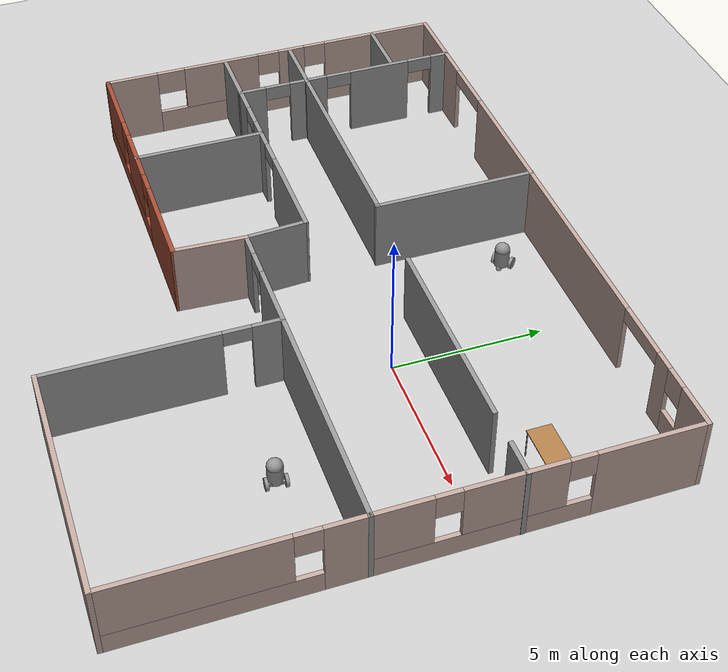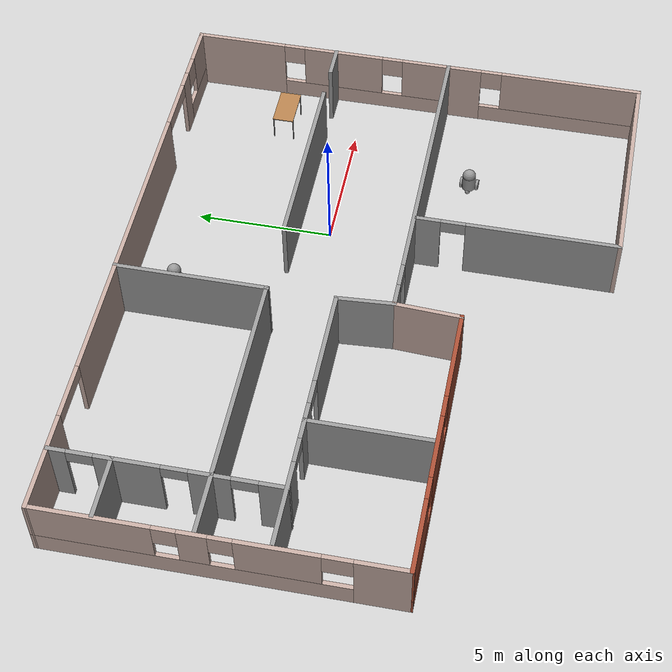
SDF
<sdf version="1.6">
 <world name="default">
  <plugin name="welcome" filename="libwelcome.so"/>
  <light name="sun" type="directional">
   <pose>0 0 10 0 -0 0</pose>
   <diffuse>0.8 0.8 0.8 1</diffuse>
   <specular>0.2 0.2 0.2 1</specular>
   <attenuation>
    <range>1000</range>
    <constant>0.9</constant>
    <linear>0.01</linear>
    <quadratic>0.001</quadratic>
   </attenuation>
   <direction>-0.5 0.1 -0.9</direction>
  </light>
  <model name="ground_plane">
   <static>1</static>
   <link name="link">
    <collision name="collision">
     <geometry><plane><normal>0 0 1</normal><size>100 100</size></plane></geometry>
     <surface><friction><ode><mu>100</mu><mu2>50</mu2></ode></friction></surface>
    </collision>
    <visual name="visual">
     <cast_shadows>0</cast_shadows>
     <geometry><plane><normal>0 0 1</normal><size>100 100</size></plane></geometry>
     <material>
      <script><uri>file://media/materials/scripts/gazebo.material</uri><name>Gazebo/Grey</name></script>
     </material>
    </visual>
   </link>
  </model>
  <gravity>0 0 -9.8</gravity>
  <magnetic_field>6e-06 2.3e-05 -4.2e-05</magnetic_field>
  <atmosphere type="adiabatic"/>
  <physics name="default_physics" default="0" type="ode">
   <max_step_size>0.001</max_step_size>
   <real_time_factor>1</real_time_factor>
   <real_time_update_rate>1000</real_time_update_rate>
  </physics>
  <scene><ambient>0.4 0.4 0.4 1</ambient><background>0.7 0.7 0.7 1</background><shadows>1</shadows></scene>
  <spherical_coordinates>
   <surface_model>EARTH_WGS84</surface_model>
   <latitude_deg>0</latitude_deg>
   <longitude_deg>0</longitude_deg>
   <elevation>0</elevation>
   <heading_deg>0</heading_deg>
  </spherical_coordinates>
  <model name="MyHouse">
   <pose>-3.71946 -1.98455 0 0 -0 0</pose>
   <link name="Wall_10">
    <pose>-8.45774 0.74582 0 0 -0 3.14159</pose>
    <visual name="Wall_10_Visual_0">
     <pose>-1.97921 0 1.25 0 -0 0</pose>
     <geometry><box><size>0.791588 0.15 2.5</size></box></geometry>
     <material>
      <script><uri>file://media/materials/scripts/gazebo.material</uri><name>Gazebo/Grey</name></script>
      <ambient>1 1 1 1</ambient>
     </material>
     <meta><layer>0</layer></meta>
    </visual>
    <collision name="Wall_10_Collision_0">
     <geometry><box><size>0.791588 0.15 2.5</size></box></geometry>
     <pose>-1.97921 0 1.25 0 -0 0</pose>
    </collision>
    <visual name="Wall_10_Visual_1">
     <pose>0.845794 0 1.25 0 -0 0</pose>
     <geometry><box><size>3.05841 0.15 2.5</size></box></geometry>
     <material>
      <script><uri>file://media/materials/scripts/gazebo.material</uri><name>Gazebo/Grey</name></script>
      <ambient>1 1 1 1</ambient>
     </material>
     <meta><layer>0</layer></meta>
    </visual>
    <collision name="Wall_10_Collision_1">
     <geometry><box><size>3.05841 0.15 2.5</size></box></geometry>
     <pose>0.845794 0 1.25 0 -0 0</pose>
    </collision>
    <visual name="Wall_10_Visual_2">
     <pose>-1.13341 0 2.25 0 -0 0</pose>
     <geometry><box><size>0.9 0.15 0.5</size></box></geometry>
     <material>
      <script><uri>file://media/materials/scripts/gazebo.material</uri><name>Gazebo/Grey</name></script>
      <ambient>1 1 1 1</ambient>
     </material>
     <meta><layer>0</layer></meta>
    </visual>
    <collision name="Wall_10_Collision_2">
     <geometry><box><size>0.9 0.15 0.5</size></box></geometry>
     <pose>-1.13341 0 2.25 0 -0 0</pose>
    </collision>
   </link>
   <link name="Wall_12">
    <pose>-3.60774 0.74582 0 0 -0 0</pose>
    <visual name="Wall_12_Visual_0">
     <pose>-2.24932 0 1.25 0 -0 0</pose>
     <geometry><box><size>0.751361 0.15 2.5</size></box></geometry>
     <material>
      <script><uri>file://media/materials/scripts/gazebo.material</uri><name>Gazebo/Grey</name></script>
      <ambient>1 1 1 1</ambient>
     </material>
     <meta><layer>0</layer></meta>
    </visual>
    <collision name="Wall_12_Collision_0">
     <geometry><box><size>0.751361 0.15 2.5</size></box></geometry>
     <pose>-2.24932 0 1.25 0 -0 0</pose>
    </collision>
    <visual name="Wall_12_Visual_1">
     <pose>0.82568 0 1.25 0 -0 0</pose>
     <geometry><box><size>3.59864 0.15 2.5</size></box></geometry>
     <material>
      <script><uri>file://media/materials/scripts/gazebo.material</uri><name>Gazebo/Grey</name></script>
      <ambient>1 1 1 1</ambient>
     </material>
     <meta><layer>0</layer></meta>
    </visual>
    <collision name="Wall_12_Collision_1">
     <geometry><box><size>3.59864 0.15 2.5</size></box></geometry>
     <pose>0.82568 0 1.25 0 -0 0</pose>
    </collision>
    <visual name="Wall_12_Visual_2">
     <pose>-1.42364 0 2.25 0 -0 0</pose>
     <geometry><box><size>0.9 0.15 0.5</size></box></geometry>
     <material>
      <script><uri>file://media/materials/scripts/gazebo.material</uri><name>Gazebo/Grey</name></script>
      <ambient>1 1 1 1</ambient>
     </material>
     <meta><layer>0</layer></meta>
    </visual>
    <collision name="Wall_12_Collision_2">
     <geometry><box><size>0.9 0.15 0.5</size></box></geometry>
     <pose>-1.42364 0 2.25 0 -0 0</pose>
    </collision>
   </link>
   <link name="Wall_13">
    <collision name="Wall_13_Collision">
     <geometry><box><size>2.15429 0.15 2.5</size></box></geometry>
     <pose>0 0 1.25 0 -0 0</pose>
    </collision>
    <visual name="Wall_13_Visual">
     <pose>0 0 1.25 0 -0 0</pose>
     <geometry><box><size>2.15429 0.15 2.5</size></box></geometry>
     <material>
      <script><uri>file://media/materials/scripts/gazebo.material</uri><name>Gazebo/Grey</name></script>
      <ambient>1 1 1 1</ambient>
     </material>
     <meta><layer>0</layer></meta>
    </visual>
    <pose>-0.995053 -0.254364 0 0 0 -1.5082</pose>
   </link>
   <link name="Wall_15">
    <pose>-8.75239 4.64524 0 0 -0 1.5708</pose>
    <visual name="Wall_15_Visual_0">
     <pose>-3.49358 0 1.25 0 -0 0</pose>
     <geometry><box><size>1.01284 0.15 2.5</size></box></geometry>
     <material>
      <script><uri>file://media/materials/scripts/gazebo.material</uri><name>Gazebo/Grey</name></script>
      <ambient>1 1 1 1</ambient>
     </material>
     <meta><layer>0</layer></meta>
    </visual>
    <collision name="Wall_15_Collision_0">
     <geometry><box><size>1.01284 0.15 2.5</size></box></geometry>
     <pose>-3.49358 0 1.25 0 -0 0</pose>
    </collision>
    <visual name="Wall_15_Visual_1">
     <pose>-1.39069 0 1.25 0 -0 0</pose>
     <geometry><box><size>1.39295 0.15 2.5</size></box></geometry>
     <material>
      <script><uri>file://media/materials/scripts/gazebo.material</uri><name>Gazebo/Grey</name></script>
      <ambient>1 1 1 1</ambient>
     </material>
     <meta><layer>0</layer></meta>
    </visual>
    <collision name="Wall_15_Collision_1">
     <geometry><box><size>1.39295 0.15 2.5</size></box></geometry>
     <pose>-1.39069 0 1.25 0 -0 0</pose>
    </collision>
    <visual name="Wall_15_Visual_2">
     <pose>1.31458 0 1.25 0 -0 0</pose>
     <geometry><box><size>2.2176 0.15 2.5</size></box></geometry>
     <material>
      <script><uri>file://media/materials/scripts/gazebo.material</uri><name>Gazebo/Grey</name></script>
      <ambient>1 1 1 1</ambient>
     </material>
     <meta><layer>0</layer></meta>
    </visual>
    <collision name="Wall_15_Collision_2">
     <geometry><box><size>2.2176 0.15 2.5</size></box></geometry>
     <pose>1.31458 0 1.25 0 -0 0</pose>
    </collision>
    <visual name="Wall_15_Visual_3">
     <pose>3.66169 0 1.25 0 -0 0</pose>
     <geometry><box><size>0.676613 0.15 2.5</size></box></geometry>
     <material>
      <script><uri>file://media/materials/scripts/gazebo.material</uri><name>Gazebo/Grey</name></script>
      <ambient>1 1 1 1</ambient>
     </material>
     <meta><layer>0</layer></meta>
    </visual>
    <collision name="Wall_15_Collision_3">
     <geometry><box><size>0.676613 0.15 2.5</size></box></geometry>
     <pose>3.66169 0 1.25 0 -0 0</pose>
    </collision>
    <visual name="Wall_15_Visual_4">
     <pose>-2.53716 0 2.25 0 -0 0</pose>
     <geometry><box><size>0.9 0.15 0.5</size></box></geometry>
     <material>
      <script><uri>file://media/materials/scripts/gazebo.material</uri><name>Gazebo/Grey</name></script>
      <ambient>1 1 1 1</ambient>
     </material>
     <meta><layer>0</layer></meta>
    </visual>
    <collision name="Wall_15_Collision_4">
     <geometry><box><size>0.9 0.15 0.5</size></box></geometry>
     <pose>-2.53716 0 2.25 0 -0 0</pose>
    </collision>
    <visual name="Wall_15_Visual_5">
     <pose>-0.244216 0 2.25 0 -0 0</pose>
     <geometry><box><size>0.9 0.15 0.5</size></box></geometry>
     <material>
      <script><uri>file://media/materials/scripts/gazebo.material</uri><name>Gazebo/Grey</name></script>
      <ambient>1 1 1 1</ambient>
     </material>
     <meta><layer>0</layer></meta>
    </visual>
    <collision name="Wall_15_Collision_5">
     <geometry><box><size>0.9 0.15 0.5</size></box></geometry>
     <pose>-0.244216 0 2.25 0 -0 0</pose>
    </collision>
    <visual name="Wall_15_Visual_6">
     <pose>2.87339 0 2.25 0 -0 0</pose>
     <geometry><box><size>0.9 0.15 0.5</size></box></geometry>
     <material>
      <script><uri>file://media/materials/scripts/gazebo.material</uri><name>Gazebo/Grey</name></script>
      <ambient>1 1 1 1</ambient>
     </material>
     <meta><layer>0</layer></meta>
    </visual>
    <collision name="Wall_15_Collision_6">
     <geometry><box><size>0.9 0.15 0.5</size></box></geometry>
     <pose>2.87339 0 2.25 0 -0 0</pose>
    </collision>
   </link>
   <link name="Wall_17">
    <collision name="Wall_17_Collision">
     <geometry><box><size>7.75 0.15 2.5</size></box></geometry>
     <pose>0 0 1.25 0 -0 0</pose>
    </collision>
    <visual name="Wall_17_Visual">
     <pose>0 0 1.25 0 -0 0</pose>
     <geometry><box><size>7.75 0.15 2.5</size></box></geometry>
     <material>
      <script><uri>file://media/materials/scripts/gazebo.material</uri><name>Gazebo/Grey</name></script>
      <ambient>1 1 1 1</ambient>
     </material>
     <meta><layer>0</layer></meta>
    </visual>
    <pose>-4.87194 3.19421 0 0 -0 0</pose>
   </link>
   <link name="Wall_18">
    <collision name="Wall_18_Collision">
     <geometry><box><size>5.58045 0.15 2.5</size></box></geometry>
     <pose>0 0 1.25 0 -0 0</pose>
    </collision>
    <visual name="Wall_18_Visual">
     <pose>0 0 1.25 0 -0 0</pose>
     <geometry><box><size>5.58045 0.15 2.5</size></box></geometry>
     <material>
      <script><uri>file://media/materials/scripts/gazebo.material</uri><name>Gazebo/Grey</name></script>
      <ambient>1 1 1 1</ambient>
     </material>
     <meta><layer>0</layer></meta>
    </visual>
    <pose>-1.07194 5.88932 0 0 -0 1.5708</pose>
   </link>
   <link name="Wall_2">
    <pose>-0.007362 8.59545 0 0 -0 0</pose>
    <visual name="Wall_2_Visual_0">
     <pose>-9.24484 0 1.25 0 -0 0</pose>
     <geometry><box><size>3.51031 0.15 2.5</size></box></geometry>
     <material>
      <script><uri>file://media/materials/scripts/gazebo.material</uri><name>Gazebo/Grey</name></script>
      <ambient>0.760784 0.662745 0.627451 1</ambient>
     </material>
     <meta><layer>0</layer></meta>
    </visual>
    <collision name="Wall_2_Collision_0">
     <geometry><box><size>3.51031 0.15 2.5</size></box></geometry>
     <pose>-9.24484 0 1.25 0 -0 0</pose>
    </collision>
    <visual name="Wall_2_Visual_1">
     <pose>0.256231 0 1.25 0 -0 0</pose>
     <geometry><box><size>11.4918 0.15 2.5</size></box></geometry>
     <material>
      <script><uri>file://media/materials/scripts/gazebo.material</uri><name>Gazebo/Grey</name></script>
      <ambient>0.760784 0.662745 0.627451 1</ambient>
     </material>
     <meta><layer>0</layer></meta>
    </visual>
    <collision name="Wall_2_Collision_1">
     <geometry><box><size>11.4918 0.15 2.5</size></box></geometry>
     <pose>0.256231 0 1.25 0 -0 0</pose>
    </collision>
    <visual name="Wall_2_Visual_2">
     <pose>8.34893 0 1.25 0 -0 0</pose>
     <geometry><box><size>0.693556 0.15 2.5</size></box></geometry>
     <material>
      <script><uri>file://media/materials/scripts/gazebo.material</uri><name>Gazebo/Grey</name></script>
      <ambient>0.760784 0.662745 0.627451 1</ambient>
     </material>
     <meta><layer>0</layer></meta>
    </visual>
    <collision name="Wall_2_Collision_2">
     <geometry><box><size>0.693556 0.15 2.5</size></box></geometry>
     <pose>8.34893 0 1.25 0 -0 0</pose>
    </collision>
    <visual name="Wall_2_Visual_3">
     <pose>9.84785 0 0.4 0 -0 0</pose>
     <geometry><box><size>2.3043 0.15 0.8</size></box></geometry>
     <material>
      <script><uri>file://media/materials/scripts/gazebo.material</uri><name>Gazebo/Grey</name></script>
      <ambient>0.760784 0.662745 0.627451 1</ambient>
     </material>
     <meta><layer>0</layer></meta>
    </visual>
    <collision name="Wall_2_Collision_3">
     <geometry><box><size>2.3043 0.15 0.8</size></box></geometry>
     <pose>9.84785 0 0.4 0 -0 0</pose>
    </collision>
    <visual name="Wall_2_Visual_4">
     <pose>10.2479 0 1.65 0 -0 0</pose>
     <geometry><box><size>1.50429 0.15 1.7</size></box></geometry>
     <material>
      <script><uri>file://media/materials/scripts/gazebo.material</uri><name>Gazebo/Grey</name></script>
      <ambient>0.760784 0.662745 0.627451 1</ambient>
     </material>
     <meta><layer>0</layer></meta>
    </visual>
    <collision name="Wall_2_Collision_4">
     <geometry><box><size>1.50429 0.15 1.7</size></box></geometry>
     <pose>10.2479 0 1.65 0 -0 0</pose>
    </collision>
    <visual name="Wall_2_Visual_5">
     <pose>9.09571 0 2.05 0 -0 0</pose>
     <geometry><box><size>0.8 0.15 0.9</size></box></geometry>
     <material>
      <script><uri>file://media/materials/scripts/gazebo.material</uri><name>Gazebo/Grey</name></script>
      <ambient>0.760784 0.662745 0.627451 1</ambient>
     </material>
     <meta><layer>0</layer></meta>
    </visual>
    <collision name="Wall_2_Collision_5">
     <geometry><box><size>0.8 0.15 0.9</size></box></geometry>
     <pose>9.09571 0 2.05 0 -0 0</pose>
    </collision>
    <visual name="Wall_2_Visual_6">
     <pose>-6.48969 0 2.25 0 -0 0</pose>
     <geometry><box><size>2 0.15 0.5</size></box></geometry>
     <material>
      <script><uri>file://media/materials/scripts/gazebo.material</uri><name>Gazebo/Grey</name></script>
      <ambient>0.760784 0.662745 0.627451 1</ambient>
     </material>
     <meta><layer>0</layer></meta>
    </visual>
    <collision name="Wall_2_Collision_6">
     <geometry><box><size>2 0.15 0.5</size></box></geometry>
     <pose>-6.48969 0 2.25 0 -0 0</pose>
    </collision>
    <visual name="Wall_2_Visual_7">
     <pose>7.00215 0 2.25 0 -0 0</pose>
     <geometry><box><size>2 0.15 0.5</size></box></geometry>
     <material>
      <script><uri>file://media/materials/scripts/gazebo.material</uri><name>Gazebo/Grey</name></script>
      <ambient>0.760784 0.662745 0.627451 1</ambient>
     </material>
     <meta><layer>0</layer></meta>
    </visual>
    <collision name="Wall_2_Collision_7">
     <geometry><box><size>2 0.15 0.5</size></box></geometry>
     <pose>7.00215 0 2.25 0 -0 0</pose>
    </collision>
   </link>
   <link name="Wall_20">
    <collision name="Wall_20_Collision">
     <geometry><box><size>2.25 0.15 2.5</size></box></geometry>
     <pose>0 0 1.25 0 -0 0</pose>
    </collision>
    <visual name="Wall_20_Visual">
     <pose>0 0 1.25 0 -0 0</pose>
     <geometry><box><size>2.25 0.15 2.5</size></box></geometry>
     <material>
      <script><uri>file://media/materials/scripts/gazebo.material</uri><name>Gazebo/Grey</name></script>
      <ambient>1 1 1 1</ambient>
     </material>
     <meta><layer>0</layer></meta>
    </visual>
    <pose>-9.72194 3.19421 0 0 -0 3.14159</pose>
   </link>
   <link name="Wall_23">
    <collision name="Wall_23_Collision">
     <geometry><box><size>2.25 0.15 2.5</size></box></geometry>
     <pose>0 0 1.25 0 -0 0</pose>
    </collision>
    <visual name="Wall_23_Visual">
     <pose>0 0 1.25 0 -0 0</pose>
     <geometry><box><size>2.25 0.15 2.5</size></box></geometry>
     <material>
      <script><uri>file://media/materials/scripts/gazebo.material</uri><name>Gazebo/Grey</name></script>
      <ambient>1 1 1 1</ambient>
     </material>
     <meta><layer>0</layer></meta>
    </visual>
    <pose>-9.8024 6.45261 0 0 -0 3.14159</pose>
   </link>
   <link name="Wall_25">
    <collision name="Wall_25_Collision">
     <geometry><box><size>7 0.15 2.5</size></box></geometry>
     <pose>0 0 1.25 0 -0 0</pose>
    </collision>
    <visual name="Wall_25_Visual">
     <pose>0 0 1.25 0 -0 0</pose>
     <geometry><box><size>7 0.15 2.5</size></box></geometry>
     <material>
      <script><uri>file://media/materials/scripts/gazebo.material</uri><name>Gazebo/Grey</name></script>
      <ambient>1 1 1 1</ambient>
     </material>
     <meta><layer>0</layer></meta>
    </visual>
    <pose>5.17189 3.19421 0 0 -0 0</pose>
   </link>
   <link name="Wall_27">
    <collision name="Wall_27_Collision">
     <geometry><box><size>1.25 0.15 2.5</size></box></geometry>
     <pose>0 0 1.25 0 -0 0</pose>
    </collision>
    <visual name="Wall_27_Visual">
     <pose>0 0 1.25 0 -0 0</pose>
     <geometry><box><size>1.25 0.15 2.5</size></box></geometry>
     <material>
      <script><uri>file://media/materials/scripts/gazebo.material</uri><name>Gazebo/Grey</name></script>
      <ambient>1 1 1 1</ambient>
     </material>
     <meta><layer>0</layer></meta>
    </visual>
    <pose>10.3825 3.17409 0 0 -0 0</pose>
   </link>
   <link name="Wall_29">
    <pose>10.9176 -4.92955 0 0 0 -1.5708</pose>
    <visual name="Wall_29_Visual_0">
     <pose>-3.06879 0 1.25 0 -0 0</pose>
     <geometry><box><size>1.36242 0.15 2.5</size></box></geometry>
     <material>
      <script><uri>file://media/materials/scripts/gazebo.material</uri><name>Gazebo/Grey</name></script>
      <ambient>0.760784 0.662745 0.627451 1</ambient>
     </material>
     <meta><layer>0</layer></meta>
    </visual>
    <collision name="Wall_29_Collision_0">
     <geometry><box><size>1.36242 0.15 2.5</size></box></geometry>
     <pose>-3.06879 0 1.25 0 -0 0</pose>
    </collision>
    <visual name="Wall_29_Visual_1">
     <pose>0.681209 0 0.35 0 -0 0</pose>
     <geometry><box><size>6.13758 0.15 0.7</size></box></geometry>
     <material>
      <script><uri>file://media/materials/scripts/gazebo.material</uri><name>Gazebo/Grey</name></script>
      <ambient>0.760784 0.662745 0.627451 1</ambient>
     </material>
     <meta><layer>0</layer></meta>
    </visual>
    <collision name="Wall_29_Collision_1">
     <geometry><box><size>6.13758 0.15 0.7</size></box></geometry>
     <pose>0.681209 0 0.35 0 -0 0</pose>
    </collision>
    <visual name="Wall_29_Visual_2">
     <pose>1.08121 0 1.6 0 -0 0</pose>
     <geometry><box><size>5.33758 0.15 1.8</size></box></geometry>
     <material>
      <script><uri>file://media/materials/scripts/gazebo.material</uri><name>Gazebo/Grey</name></script>
      <ambient>0.760784 0.662745 0.627451 1</ambient>
     </material>
     <meta><layer>0</layer></meta>
    </visual>
    <collision name="Wall_29_Collision_2">
     <geometry><box><size>5.33758 0.15 1.8</size></box></geometry>
     <pose>1.08121 0 1.6 0 -0 0</pose>
    </collision>
    <visual name="Wall_29_Visual_3">
     <pose>-1.98758 0 2.1 0 -0 0</pose>
     <geometry><box><size>0.8 0.15 0.8</size></box></geometry>
     <material>
      <script><uri>file://media/materials/scripts/gazebo.material</uri><name>Gazebo/Grey</name></script>
      <ambient>0.760784 0.662745 0.627451 1</ambient>
     </material>
     <meta><layer>0</layer></meta>
    </visual>
    <collision name="Wall_29_Collision_3">
     <geometry><box><size>0.8 0.15 0.8</size></box></geometry>
     <pose>-1.98758 0 2.1 0 -0 0</pose>
    </collision>
   </link>
   <link name="Wall_3">
    <pose>10.9176 3.67045 0 0 0 -1.5708</pose>
    <visual name="Wall_3_Visual_0">
     <pose>-3.27648 0 1.25 0 -0 0</pose>
     <geometry><box><size>3.44705 0.15 2.5</size></box></geometry>
     <material>
      <script><uri>file://media/materials/scripts/gazebo.material</uri><name>Gazebo/Grey</name></script>
      <ambient>0.760784 0.662745 0.627451 1</ambient>
     </material>
     <meta><layer>0</layer></meta>
    </visual>
    <collision name="Wall_3_Collision_0">
     <geometry><box><size>3.44705 0.15 2.5</size></box></geometry>
     <pose>-3.27648 0 1.25 0 -0 0</pose>
    </collision>
    <visual name="Wall_3_Visual_1">
     <pose>1.72352 0 0.35 0 -0 0</pose>
     <geometry><box><size>6.55295 0.15 0.7</size></box></geometry>
     <material>
      <script><uri>file://media/materials/scripts/gazebo.material</uri><name>Gazebo/Grey</name></script>
      <ambient>0.760784 0.662745 0.627451 1</ambient>
     </material>
     <meta><layer>0</layer></meta>
    </visual>
    <collision name="Wall_3_Collision_1">
     <geometry><box><size>6.55295 0.15 0.7</size></box></geometry>
     <pose>1.72352 0 0.35 0 -0 0</pose>
    </collision>
    <visual name="Wall_3_Visual_2">
     <pose>0.788006 0 1.6 0 -0 0</pose>
     <geometry><box><size>3.08192 0.15 1.8</size></box></geometry>
     <material>
      <script><uri>file://media/materials/scripts/gazebo.material</uri><name>Gazebo/Grey</name></script>
      <ambient>0.760784 0.662745 0.627451 1</ambient>
     </material>
     <meta><layer>0</layer></meta>
    </visual>
    <collision name="Wall_3_Collision_2">
     <geometry><box><size>3.08192 0.15 1.8</size></box></geometry>
     <pose>0.788006 0 1.6 0 -0 0</pose>
    </collision>
    <visual name="Wall_3_Visual_3">
     <pose>4.06448 0 1.6 0 -0 0</pose>
     <geometry><box><size>1.87103 0.15 1.8</size></box></geometry>
     <material>
      <script><uri>file://media/materials/scripts/gazebo.material</uri><name>Gazebo/Grey</name></script>
      <ambient>0.760784 0.662745 0.627451 1</ambient>
     </material>
     <meta><layer>0</layer></meta>
    </visual>
    <collision name="Wall_3_Collision_3">
     <geometry><box><size>1.87103 0.15 1.8</size></box></geometry>
     <pose>4.06448 0 1.6 0 -0 0</pose>
    </collision>
    <visual name="Wall_3_Visual_4">
     <pose>-1.15295 0 2.1 0 -0 0</pose>
     <geometry><box><size>0.8 0.15 0.8</size></box></geometry>
     <material>
      <script><uri>file://media/materials/scripts/gazebo.material</uri><name>Gazebo/Grey</name></script>
      <ambient>0.760784 0.662745 0.627451 1</ambient>
     </material>
     <meta><layer>0</layer></meta>
    </visual>
    <collision name="Wall_3_Collision_4">
     <geometry><box><size>0.8 0.15 0.8</size></box></geometry>
     <pose>-1.15295 0 2.1 0 -0 0</pose>
    </collision>
    <visual name="Wall_3_Visual_5">
     <pose>2.72897 0 2.1 0 -0 0</pose>
     <geometry><box><size>0.8 0.15 0.8</size></box></geometry>
     <material>
      <script><uri>file://media/materials/scripts/gazebo.material</uri><name>Gazebo/Grey</name></script>
      <ambient>0.760784 0.662745 0.627451 1</ambient>
     </material>
     <meta><layer>0</layer></meta>
    </visual>
    <collision name="Wall_3_Collision_5">
     <geometry><box><size>0.8 0.15 0.8</size></box></geometry>
     <pose>2.72897 0 2.1 0 -0 0</pose>
    </collision>
   </link>
   <link name="Wall_30">
    <collision name="Wall_30_Collision">
     <geometry><box><size>8 0.15 2.5</size></box></geometry>
     <pose>0 0 1.25 0 -0 0</pose>
    </collision>
    <visual name="Wall_30_Visual">
     <pose>0 0 1.25 0 -0 0</pose>
     <geometry><box><size>8 0.15 2.5</size></box></geometry>
     <material>
      <script><uri>file://media/materials/scripts/gazebo.material</uri><name>Gazebo/Grey</name></script>
      <ambient>0.760784 0.662745 0.627451 1</ambient>
     </material>
     <meta><layer>0</layer></meta>
    </visual>
    <pose>6.99264 -8.60455 0 0 -0 3.14159</pose>
   </link>
   <link name="Wall_31">
    <pose>3.06764 -4.92955 0 0 -0 1.5708</pose>
    <visual name="Wall_31_Visual_0">
     <pose>-0.966637 0 1.25 0 -0 0</pose>
     <geometry><box><size>5.56673 0.15 2.5</size></box></geometry>
     <material>
      <script><uri>file://media/materials/scripts/gazebo.material</uri><name>Gazebo/Grey</name></script>
      <ambient>1 1 1 1</ambient>
     </material>
     <meta><layer>0</layer></meta>
    </visual>
    <collision name="Wall_31_Collision_0">
     <geometry><box><size>5.56673 0.15 2.5</size></box></geometry>
     <pose>-0.966637 0 1.25 0 -0 0</pose>
    </collision>
    <visual name="Wall_31_Visual_1">
     <pose>3.23336 0 1.25 0 -0 0</pose>
     <geometry><box><size>1.03327 0.15 2.5</size></box></geometry>
     <material>
      <script><uri>file://media/materials/scripts/gazebo.material</uri><name>Gazebo/Grey</name></script>
      <ambient>1 1 1 1</ambient>
     </material>
     <meta><layer>0</layer></meta>
    </visual>
    <collision name="Wall_31_Collision_1">
     <geometry><box><size>1.03327 0.15 2.5</size></box></geometry>
     <pose>3.23336 0 1.25 0 -0 0</pose>
    </collision>
    <visual name="Wall_31_Visual_2">
     <pose>2.26673 0 2.25 0 -0 0</pose>
     <geometry><box><size>0.9 0.15 0.5</size></box></geometry>
     <material>
      <script><uri>file://media/materials/scripts/gazebo.material</uri><name>Gazebo/Grey</name></script>
      <ambient>1 1 1 1</ambient>
     </material>
     <meta><layer>0</layer></meta>
    </visual>
    <collision name="Wall_31_Collision_2">
     <geometry><box><size>0.9 0.15 0.5</size></box></geometry>
     <pose>2.26673 0 2.25 0 -0 0</pose>
    </collision>
   </link>
   <link name="Wall_4">
    <pose>4.99264 -1.25455 0 0 -0 3.14159</pose>
    <visual name="Wall_4_Visual_0">
     <pose>-0.913533 0 1.25 0 -0 0</pose>
     <geometry><box><size>10.1729 0.15 2.5</size></box></geometry>
     <material>
      <script><uri>file://media/materials/scripts/gazebo.material</uri><name>Gazebo/Grey</name></script>
      <ambient>1 1 1 1</ambient>
     </material>
     <meta><layer>0</layer></meta>
    </visual>
    <collision name="Wall_4_Collision_0">
     <geometry><box><size>10.1729 0.15 2.5</size></box></geometry>
     <pose>-0.913533 0 1.25 0 -0 0</pose>
    </collision>
    <visual name="Wall_4_Visual_1">
     <pose>5.53647 0 1.25 0 -0 0</pose>
     <geometry><box><size>0.927067 0.15 2.5</size></box></geometry>
     <material>
      <script><uri>file://media/materials/scripts/gazebo.material</uri><name>Gazebo/Grey</name></script>
      <ambient>1 1 1 1</ambient>
     </material>
     <meta><layer>0</layer></meta>
    </visual>
    <collision name="Wall_4_Collision_1">
     <geometry><box><size>0.927067 0.15 2.5</size></box></geometry>
     <pose>5.53647 0 1.25 0 -0 0</pose>
    </collision>
    <visual name="Wall_4_Visual_2">
     <pose>4.62293 0 2.25 0 -0 0</pose>
     <geometry><box><size>0.9 0.15 0.5</size></box></geometry>
     <material>
      <script><uri>file://media/materials/scripts/gazebo.material</uri><name>Gazebo/Grey</name></script>
      <ambient>1 1 1 1</ambient>
     </material>
     <meta><layer>0</layer></meta>
    </visual>
    <collision name="Wall_4_Collision_2">
     <geometry><box><size>0.9 0.15 0.5</size></box></geometry>
     <pose>4.62293 0 2.25 0 -0 0</pose>
    </collision>
   </link>
   <link name="Wall_5">
    <collision name="Wall_5_Collision">
     <geometry><box><size>2.50297 0.15 2.5</size></box></geometry>
     <pose>0 0 1.25 0 -0 0</pose>
    </collision>
    <visual name="Wall_5_Visual">
     <pose>0 0 1.25 0 -0 0</pose>
     <geometry><box><size>2.50297 0.15 2.5</size></box></geometry>
     <material>
      <script><uri>file://media/materials/scripts/gazebo.material</uri><name>Gazebo/Grey</name></script>
      <ambient>0.760784 0.662745 0.627451 1</ambient>
     </material>
     <meta><layer>0</layer></meta>
    </visual>
    <pose>-0.992458 -2.4295 0 0 0 -1.6219</pose>
   </link>
   <link name="Wall_6">
    <pose>-5.97755 -3.60445 0 0 -0 3.14159</pose>
    <visual name="Wall_6_Visual_0">
     <pose>-3.30088 0 1.25 0 -0 0</pose>
     <geometry><box><size>3.39823 0.15 2.5</size></box></geometry>
     <material>
      <script><uri>file://media/materials/scripts/gazebo.material</uri><name>Gazebo/Bricks</name></script>
      <ambient>1 1 1 1</ambient>
     </material>
     <meta><layer>0</layer></meta>
    </visual>
    <collision name="Wall_6_Collision_0">
     <geometry><box><size>3.39823 0.15 2.5</size></box></geometry>
     <pose>-3.30088 0 1.25 0 -0 0</pose>
    </collision>
    <visual name="Wall_6_Visual_1">
     <pose>1.69912 0 0.35 0 -0 0</pose>
     <geometry><box><size>6.60177 0.15 0.7</size></box></geometry>
     <material>
      <script><uri>file://media/materials/scripts/gazebo.material</uri><name>Gazebo/Bricks</name></script>
      <ambient>1 1 1 1</ambient>
     </material>
     <meta><layer>0</layer></meta>
    </visual>
    <collision name="Wall_6_Collision_1">
     <geometry><box><size>6.60177 0.15 0.7</size></box></geometry>
     <pose>1.69912 0 0.35 0 -0 0</pose>
    </collision>
    <visual name="Wall_6_Visual_2">
     <pose>0.37341 0 1.6 0 -0 0</pose>
     <geometry><box><size>2.35035 0.15 1.8</size></box></geometry>
     <material>
      <script><uri>file://media/materials/scripts/gazebo.material</uri><name>Gazebo/Bricks</name></script>
      <ambient>1 1 1 1</ambient>
     </material>
     <meta><layer>0</layer></meta>
    </visual>
    <collision name="Wall_6_Collision_2">
     <geometry><box><size>2.35035 0.15 1.8</size></box></geometry>
     <pose>0.37341 0 1.6 0 -0 0</pose>
    </collision>
    <visual name="Wall_6_Visual_3">
     <pose>3.67429 0 1.6 0 -0 0</pose>
     <geometry><box><size>2.65141 0.15 1.8</size></box></geometry>
     <material>
      <script><uri>file://media/materials/scripts/gazebo.material</uri><name>Gazebo/Bricks</name></script>
      <ambient>1 1 1 1</ambient>
     </material>
     <meta><layer>0</layer></meta>
    </visual>
    <collision name="Wall_6_Collision_3">
     <geometry><box><size>2.65141 0.15 1.8</size></box></geometry>
     <pose>3.67429 0 1.6 0 -0 0</pose>
    </collision>
    <visual name="Wall_6_Visual_4">
     <pose>-1.20177 0 2.1 0 -0 0</pose>
     <geometry><box><size>0.8 0.15 0.8</size></box></geometry>
     <material>
      <script><uri>file://media/materials/scripts/gazebo.material</uri><name>Gazebo/Bricks</name></script>
      <ambient>1 1 1 1</ambient>
     </material>
     <meta><layer>0</layer></meta>
    </visual>
    <collision name="Wall_6_Collision_4">
     <geometry><box><size>0.8 0.15 0.8</size></box></geometry>
     <pose>-1.20177 0 2.1 0 -0 0</pose>
    </collision>
    <visual name="Wall_6_Visual_5">
     <pose>1.94859 0 2.1 0 -0 0</pose>
     <geometry><box><size>0.8 0.15 0.8</size></box></geometry>
     <material>
      <script><uri>file://media/materials/scripts/gazebo.material</uri><name>Gazebo/Bricks</name></script>
      <ambient>1 1 1 1</ambient>
     </material>
     <meta><layer>0</layer></meta>
    </visual>
    <collision name="Wall_6_Collision_5">
     <geometry><box><size>0.8 0.15 0.8</size></box></geometry>
     <pose>1.94859 0 2.1 0 -0 0</pose>
    </collision>
   </link>
   <link name="Wall_7">
    <pose>-10.9175 2.4955 0 0 -0 1.57324</pose>
    <visual name="Wall_7_Visual_0">
     <pose>-5.23558 0 1.25 0 -0 0</pose>
     <geometry><box><size>1.87887 0.15 2.5</size></box></geometry>
     <material>
      <script><uri>file://media/materials/scripts/gazebo.material</uri><name>Gazebo/Grey</name></script>
      <ambient>0.760784 0.662745 0.627451 1</ambient>
     </material>
     <meta><layer>0</layer></meta>
    </visual>
    <collision name="Wall_7_Collision_0">
     <geometry><box><size>1.87887 0.15 2.5</size></box></geometry>
     <pose>-5.23558 0 1.25 0 -0 0</pose>
    </collision>
    <visual name="Wall_7_Visual_1">
     <pose>0.939435 0 0.425 0 -0 0</pose>
     <geometry><box><size>10.4712 0.15 0.85</size></box></geometry>
     <material>
      <script><uri>file://media/materials/scripts/gazebo.material</uri><name>Gazebo/Grey</name></script>
      <ambient>0.760784 0.662745 0.627451 1</ambient>
     </material>
     <meta><layer>0</layer></meta>
    </visual>
    <collision name="Wall_7_Collision_1">
     <geometry><box><size>10.4712 0.15 0.85</size></box></geometry>
     <pose>0.939435 0 0.425 0 -0 0</pose>
    </collision>
    <visual name="Wall_7_Visual_2">
     <pose>-1.90728 0 1.675 0 -0 0</pose>
     <geometry><box><size>2.77773 0.15 1.65</size></box></geometry>
     <material>
      <script><uri>file://media/materials/scripts/gazebo.material</uri><name>Gazebo/Grey</name></script>
      <ambient>0.760784 0.662745 0.627451 1</ambient>
     </material>
     <meta><layer>0</layer></meta>
    </visual>
    <collision name="Wall_7_Collision_2">
     <geometry><box><size>2.77773 0.15 1.65</size></box></geometry>
     <pose>-1.90728 0 1.675 0 -0 0</pose>
    </collision>
    <visual name="Wall_7_Visual_3">
     <pose>0.772042 0 1.675 0 -0 0</pose>
     <geometry><box><size>0.980926 0.15 1.65</size></box></geometry>
     <material>
      <script><uri>file://media/materials/scripts/gazebo.material</uri><name>Gazebo/Grey</name></script>
      <ambient>0.760784 0.662745 0.627451 1</ambient>
     </material>
     <meta><layer>0</layer></meta>
    </visual>
    <collision name="Wall_7_Collision_3">
     <geometry><box><size>0.980926 0.15 1.65</size></box></geometry>
     <pose>0.772042 0 1.675 0 -0 0</pose>
    </collision>
    <visual name="Wall_7_Visual_4">
     <pose>4.11876 0 1.675 0 -0 0</pose>
     <geometry><box><size>4.11251 0.15 1.65</size></box></geometry>
     <material>
      <script><uri>file://media/materials/scripts/gazebo.material</uri><name>Gazebo/Grey</name></script>
      <ambient>0.760784 0.662745 0.627451 1</ambient>
     </material>
     <meta><layer>0</layer></meta>
    </visual>
    <collision name="Wall_7_Collision_4">
     <geometry><box><size>4.11251 0.15 1.65</size></box></geometry>
     <pose>4.11876 0 1.675 0 -0 0</pose>
    </collision>
    <visual name="Wall_7_Visual_5">
     <pose>-3.79615 0 2.075 0 -0 0</pose>
     <geometry><box><size>1 0.15 0.85</size></box></geometry>
     <material>
      <script><uri>file://media/materials/scripts/gazebo.material</uri><name>Gazebo/Grey</name></script>
      <ambient>0.760784 0.662745 0.627451 1</ambient>
     </material>
     <meta><layer>0</layer></meta>
    </visual>
    <collision name="Wall_7_Collision_5">
     <geometry><box><size>1 0.15 0.85</size></box></geometry>
     <pose>-3.79615 0 2.075 0 -0 0</pose>
    </collision>
    <visual name="Wall_7_Visual_6">
     <pose>-0.118421 0 2.075 0 -0 0</pose>
     <geometry><box><size>0.8 0.15 0.85</size></box></geometry>
     <material>
      <script><uri>file://media/materials/scripts/gazebo.material</uri><name>Gazebo/Grey</name></script>
      <ambient>0.760784 0.662745 0.627451 1</ambient>
     </material>
     <meta><layer>0</layer></meta>
    </visual>
    <collision name="Wall_7_Collision_6">
     <geometry><box><size>0.8 0.15 0.85</size></box></geometry>
     <pose>-0.118421 0 2.075 0 -0 0</pose>
    </collision>
    <visual name="Wall_7_Visual_7">
     <pose>1.66251 0 2.075 0 -0 0</pose>
     <geometry><box><size>0.8 0.15 0.85</size></box></geometry>
     <material>
      <script><uri>file://media/materials/scripts/gazebo.material</uri><name>Gazebo/Grey</name></script>
      <ambient>0.760784 0.662745 0.627451 1</ambient>
     </material>
     <meta><layer>0</layer></meta>
    </visual>
    <collision name="Wall_7_Collision_7">
     <geometry><box><size>0.8 0.15 0.85</size></box></geometry>
     <pose>1.66251 0 2.075 0 -0 0</pose>
    </collision>
   </link>
   <link name="Wall_9">
    <collision name="Wall_9_Collision">
     <geometry><box><size>4.5 0.15 2.5</size></box></geometry>
     <pose>0 0 1.25 0 -0 0</pose>
    </collision>
    <visual name="Wall_9_Visual">
     <pose>0 0 1.25 0 -0 0</pose>
     <geometry><box><size>4.5 0.15 2.5</size></box></geometry>
     <material>
      <script><uri>file://media/materials/scripts/gazebo.material</uri><name>Gazebo/Grey</name></script>
      <ambient>1 1 1 1</ambient>
     </material>
     <meta><layer>0</layer></meta>
    </visual>
    <pose>-6.15775 -1.42918 0 0 -0 1.5708</pose>
   </link>
   <static>1</static>
  </model>
  <model name="table">
   <static>1</static>
   <link name="link">
    <collision name="surface">
     <pose>0 0 1 0 -0 0</pose>
     <geometry><box><size>1.5 0.8 0.03</size></box></geometry>
     <surface><friction><ode><mu>0.6</mu><mu2>0.6</mu2></ode></friction></surface>
    </collision>
    <visual name="visual1">
     <pose>0 0 1 0 -0 0</pose>
     <geometry><box><size>1.5 0.8 0.03</size></box></geometry>
     <material>
      <script><uri>file://media/materials/scripts/gazebo.material</uri><name>Gazebo/Wood</name></script>
     </material>
    </visual>
    <collision name="front_left_leg">
     <pose>0.68 0.38 0.5 0 -0 0</pose>
     <geometry><cylinder><radius>0.02</radius><length>1</length></cylinder></geometry>
    </collision>
    <visual name="front_left_leg">
     <pose>0.68 0.38 0.5 0 -0 0</pose>
     <geometry><cylinder><radius>0.02</radius><length>1</length></cylinder></geometry>
     <material>
      <script><uri>file://media/materials/scripts/gazebo.material</uri><name>Gazebo/Grey</name></script>
     </material>
    </visual>
    <collision name="front_right_leg">
     <pose>0.68 -0.38 0.5 0 -0 0</pose>
     <geometry><cylinder><radius>0.02</radius><length>1</length></cylinder></geometry>
    </collision>
    <visual name="front_right_leg">
     <pose>0.68 -0.38 0.5 0 -0 0</pose>
     <geometry><cylinder><radius>0.02</radius><length>1</length></cylinder></geometry>
     <material>
      <script><uri>file://media/materials/scripts/gazebo.material</uri><name>Gazebo/Grey</name></script>
     </material>
    </visual>
    <collision name="back_right_leg">
     <pose>-0.68 -0.38 0.5 0 -0 0</pose>
     <geometry><cylinder><radius>0.02</radius><length>1</length></cylinder></geometry>
    </collision>
    <visual name="back_right_leg">
     <pose>-0.68 -0.38 0.5 0 -0 0</pose>
     <geometry><cylinder><radius>0.02</radius><length>1</length></cylinder></geometry>
     <material>
      <script><uri>file://media/materials/scripts/gazebo.material</uri><name>Gazebo/Grey</name></script>
     </material>
    </visual>
    <collision name="back_left_leg">
     <pose>-0.68 0.38 0.5 0 -0 0</pose>
     <geometry><cylinder><radius>0.02</radius><length>1</length></cylinder></geometry>
    </collision>
    <visual name="back_left_leg">
     <pose>-0.68 0.38 0.5 0 -0 0</pose>
     <geometry><cylinder><radius>0.02</radius><length>1</length></cylinder></geometry>
     <material>
      <script><uri>file://media/materials/scripts/gazebo.material</uri><name>Gazebo/Grey</name></script>
     </material>
    </visual>
   </link>
   <pose>5.3462 2.80195 0 0 -0 0</pose>
  </model>
  <model name="RobotOne">
   <link name="link_0">
    <pose>-0.028333 -0 0.133333 0 -0 0</pose>
    <inertial>
     <mass>1</mass>
     <inertia><ixx>0.145833</ixx><ixy>0</ixy><ixz>0</ixz><iyy>0.145833</iyy><iyz>0</iyz><izz>0.125</izz></inertia>
    </inertial>
    <visual name="visual">
     <geometry><cylinder><radius>0.25</radius><length>0.6</length></cylinder></geometry>
     <material>
      <lighting>1</lighting>
      <script><uri>file://media/materials/scripts/gazebo.material</uri><name>Gazebo/Grey</name></script>
      <shader type="pixel"><normal_map>__default__</normal_map></shader>
      <ambient>0.3 0.3 0.3 1</ambient>
      <diffuse>0.7 0.7 0.7 1</diffuse>
      <specular>0.01 0.01 0.01 1</specular>
      <emissive>0 0 0 1</emissive>
     </material>
    </visual>
    <collision name="collision">
     <geometry><cylinder><radius>0.25</radius><length>0.6</length></cylinder></geometry>
     <surface>
      <friction>
       <ode><mu>1</mu><mu2>1</mu2><fdir1>0 0 0</fdir1><slip1>0</slip1><slip2>0</slip2></ode>
       <torsional>
        <coefficient>1</coefficient>
        <patch_radius>0</patch_radius>
        <surface_radius>0</surface_radius>
        <use_patch_radius>1</use_patch_radius>
        <ode><slip>0</slip></ode>
       </torsional>
      </friction>
      <bounce><restitution_coefficient>0</restitution_coefficient><threshold>1e+06</threshold></bounce>
      <contact>
       <collide_without_contact>0</collide_without_contact>
       <collide_without_contact_bitmask>1</collide_without_contact_bitmask>
       <collide_bitmask>1</collide_bitmask>
       <ode>
        <soft_cfm>0</soft_cfm>
        <soft_erp>0.2</soft_erp>
        <kp>1e+13</kp>
        <kd>1</kd>
        <max_vel>0.01</max_vel>
        <min_depth>0</min_depth>
       </ode>
       <bullet>
        <split_impulse>1</split_impulse>
        <split_impulse_penetration_threshold>-0.01</split_impulse_penetration_threshold>
        <soft_cfm>0</soft_cfm>
        <soft_erp>0.2</soft_erp>
        <kp>1e+13</kp>
        <kd>1</kd>
       </bullet>
      </contact>
     </surface>
    </collision>
   </link>
   <link name="link_1">
    <pose>0.081667 -0 -0.116667 0 -0 0</pose>
    <inertial>
     <mass>1</mass>
     <inertia>
      <ixx>0.166667</ixx>
      <ixy>0</ixy>
      <ixz>0</ixz>
      <iyy>0.166667</iyy>
      <iyz>0</iyz>
      <izz>0.166667</izz>
     </inertia>
    </inertial>
    <visual name="visual">
     <geometry><box><size>0.2 0.5 0.1</size></box></geometry>
     <material>
      <lighting>1</lighting>
      <script><uri>file://media/materials/scripts/gazebo.material</uri><name>Gazebo/Grey</name></script>
      <shader type="pixel"><normal_map>__default__</normal_map></shader>
      <ambient>0.3 0.3 0.3 1</ambient>
      <diffuse>0.7 0.7 0.7 1</diffuse>
      <specular>0.01 0.01 0.01 1</specular>
      <emissive>0 0 0 1</emissive>
     </material>
    </visual>
    <collision name="collision">
     <geometry><box><size>0.2 0.5 0.1</size></box></geometry>
     <surface>
      <friction>
       <ode><mu>1</mu><mu2>1</mu2><fdir1>0 0 0</fdir1><slip1>0</slip1><slip2>0</slip2></ode>
       <torsional>
        <coefficient>1</coefficient>
        <patch_radius>0</patch_radius>
        <surface_radius>0</surface_radius>
        <use_patch_radius>1</use_patch_radius>
        <ode><slip>0</slip></ode>
       </torsional>
      </friction>
      <bounce><restitution_coefficient>0</restitution_coefficient><threshold>1e+06</threshold></bounce>
      <contact>
       <collide_without_contact>0</collide_without_contact>
       <collide_without_contact_bitmask>1</collide_without_contact_bitmask>
       <collide_bitmask>1</collide_bitmask>
       <ode>
        <soft_cfm>0</soft_cfm>
        <soft_erp>0.2</soft_erp>
        <kp>1e+13</kp>
        <kd>1</kd>
        <max_vel>0.01</max_vel>
        <min_depth>0</min_depth>
       </ode>
       <bullet>
        <split_impulse>1</split_impulse>
        <split_impulse_penetration_threshold>-0.01</split_impulse_penetration_threshold>
        <soft_cfm>0</soft_cfm>
        <soft_erp>0.2</soft_erp>
        <kp>1e+13</kp>
        <kd>1</kd>
       </bullet>
      </contact>
     </surface>
    </collision>
   </link>
   <link name="link_2">
    <pose>0.101667 -0.300019 -0.116667 1.5707 -0 0</pose>
    <inertial>
     <mass>1</mass>
     <inertia><ixx>0.145833</ixx><ixy>0</ixy><ixz>0</ixz><iyy>0.145833</iyy><iyz>0</iyz><izz>0.125</izz></inertia>
    </inertial>
    <visual name="visual">
     <geometry><cylinder><radius>0.2</radius><length>0.1</length></cylinder></geometry>
     <material>
      <lighting>1</lighting>
      <script><uri>file://media/materials/scripts/gazebo.material</uri><name>Gazebo/Grey</name></script>
      <shader type="pixel"><normal_map>__default__</normal_map></shader>
      <ambient>0.3 0.3 0.3 1</ambient>
      <diffuse>0.7 0.7 0.7 1</diffuse>
      <specular>0.01 0.01 0.01 1</specular>
      <emissive>0 0 0 1</emissive>
     </material>
    </visual>
    <collision name="collision">
     <geometry><cylinder><radius>0.2</radius><length>0.1</length></cylinder></geometry>
     <surface>
      <friction>
       <ode><mu>1</mu><mu2>1</mu2><fdir1>0 0 0</fdir1><slip1>0</slip1><slip2>0</slip2></ode>
       <torsional>
        <coefficient>1</coefficient>
        <patch_radius>0</patch_radius>
        <surface_radius>0</surface_radius>
        <use_patch_radius>1</use_patch_radius>
        <ode><slip>0</slip></ode>
       </torsional>
      </friction>
      <bounce><restitution_coefficient>0</restitution_coefficient><threshold>1e+06</threshold></bounce>
      <contact>
       <collide_without_contact>0</collide_without_contact>
       <collide_without_contact_bitmask>1</collide_without_contact_bitmask>
       <collide_bitmask>1</collide_bitmask>
       <ode>
        <soft_cfm>0</soft_cfm>
        <soft_erp>0.2</soft_erp>
        <kp>1e+13</kp>
        <kd>1</kd>
        <max_vel>0.01</max_vel>
        <min_depth>0</min_depth>
       </ode>
       <bullet>
        <split_impulse>1</split_impulse>
        <split_impulse_penetration_threshold>-0.01</split_impulse_penetration_threshold>
        <soft_cfm>0</soft_cfm>
        <soft_erp>0.2</soft_erp>
        <kp>1e+13</kp>
        <kd>1</kd>
       </bullet>
      </contact>
     </surface>
    </collision>
   </link>
   <link name="link_2_clone">
    <pose>0.101667 0.300019 -0.116667 1.5707 -0 0</pose>
    <inertial>
     <mass>1</mass>
     <inertia><ixx>0.145833</ixx><ixy>0</ixy><ixz>0</ixz><iyy>0.145833</iyy><iyz>0</iyz><izz>0.125</izz></inertia>
    </inertial>
    <visual name="visual">
     <geometry><cylinder><radius>0.2</radius><length>0.1</length></cylinder></geometry>
     <material>
      <lighting>1</lighting>
      <script><uri>file://media/materials/scripts/gazebo.material</uri><name>Gazebo/Grey</name></script>
      <shader type="pixel"><normal_map>__default__</normal_map></shader>
      <ambient>0.3 0.3 0.3 1</ambient>
      <diffuse>0.7 0.7 0.7 1</diffuse>
      <specular>0.01 0.01 0.01 1</specular>
      <emissive>0 0 0 1</emissive>
     </material>
    </visual>
    <collision name="collision">
     <geometry><cylinder><radius>0.2</radius><length>0.1</length></cylinder></geometry>
     <surface>
      <friction>
       <ode><mu>1</mu><mu2>1</mu2><fdir1>0 0 0</fdir1><slip1>0</slip1><slip2>0</slip2></ode>
       <torsional>
        <coefficient>1</coefficient>
        <patch_radius>0</patch_radius>
        <surface_radius>0</surface_radius>
        <use_patch_radius>1</use_patch_radius>
        <ode><slip>0</slip></ode>
       </torsional>
      </friction>
      <bounce><restitution_coefficient>0</restitution_coefficient><threshold>1e+06</threshold></bounce>
      <contact>
       <collide_without_contact>0</collide_without_contact>
       <collide_without_contact_bitmask>1</collide_without_contact_bitmask>
       <collide_bitmask>1</collide_bitmask>
       <ode>
        <soft_cfm>0</soft_cfm>
        <soft_erp>0.2</soft_erp>
        <kp>1e+13</kp>
        <kd>1</kd>
        <max_vel>0.01</max_vel>
        <min_depth>0</min_depth>
       </ode>
       <bullet>
        <split_impulse>1</split_impulse>
        <split_impulse_penetration_threshold>-0.01</split_impulse_penetration_threshold>
        <soft_cfm>0</soft_cfm>
        <soft_erp>0.2</soft_erp>
        <kp>1e+13</kp>
        <kd>1</kd>
       </bullet>
      </contact>
     </surface>
    </collision>
   </link>
   <link name="link_3">
    <pose>-0.228333 -0 -0.216667 0 -0 0</pose>
    <inertial>
     <mass>1</mass>
     <inertia><ixx>0.1</ixx><ixy>0</ixy><ixz>0</ixz><iyy>0.1</iyy><iyz>0</iyz><izz>0.1</izz></inertia>
    </inertial>
    <visual name="visual">
     <geometry><sphere><radius>0.1</radius></sphere></geometry>
     <material>
      <lighting>1</lighting>
      <script><uri>file://media/materials/scripts/gazebo.material</uri><name>Gazebo/Grey</name></script>
      <shader type="pixel"><normal_map>__default__</normal_map></shader>
      <ambient>0.3 0.3 0.3 1</ambient>
      <diffuse>0.7 0.7 0.7 1</diffuse>
      <specular>0.01 0.01 0.01 1</specular>
      <emissive>0 0 0 1</emissive>
     </material>
    </visual>
    <collision name="collision">
     <geometry><sphere><radius>0.1</radius></sphere></geometry>
     <surface>
      <friction>
       <ode><mu>1</mu><mu2>1</mu2><fdir1>0 0 0</fdir1><slip1>0</slip1><slip2>0</slip2></ode>
       <torsional>
        <coefficient>1</coefficient>
        <patch_radius>0</patch_radius>
        <surface_radius>0</surface_radius>
        <use_patch_radius>1</use_patch_radius>
        <ode><slip>0</slip></ode>
       </torsional>
      </friction>
      <bounce><restitution_coefficient>0</restitution_coefficient><threshold>1e+06</threshold></bounce>
      <contact>
       <collide_without_contact>0</collide_without_contact>
       <collide_without_contact_bitmask>1</collide_without_contact_bitmask>
       <collide_bitmask>1</collide_bitmask>
       <ode>
        <soft_cfm>0</soft_cfm>
        <soft_erp>0.2</soft_erp>
        <kp>1e+13</kp>
        <kd>1</kd>
        <max_vel>0.01</max_vel>
        <min_depth>0</min_depth>
       </ode>
       <bullet>
        <split_impulse>1</split_impulse>
        <split_impulse_penetration_threshold>-0.01</split_impulse_penetration_threshold>
        <soft_cfm>0</soft_cfm>
        <soft_erp>0.2</soft_erp>
        <kp>1e+13</kp>
        <kd>1</kd>
       </bullet>
      </contact>
     </surface>
    </collision>
   </link>
   <link name="link_4">
    <pose>-0.028333 -0 0.433333 0 -0 0</pose>
    <inertial>
     <mass>1</mass>
     <inertia><ixx>0.1</ixx><ixy>0</ixy><ixz>0</ixz><iyy>0.1</iyy><iyz>0</iyz><izz>0.1</izz></inertia>
    </inertial>
    <visual name="visual">
     <geometry><sphere><radius>0.25</radius></sphere></geometry>
     <material>
      <lighting>1</lighting>
      <script><uri>file://media/materials/scripts/gazebo.material</uri><name>Gazebo/Grey</name></script>
      <shader type="pixel"><normal_map>__default__</normal_map></shader>
      <ambient>0.3 0.3 0.3 1</ambient>
      <diffuse>0.7 0.7 0.7 1</diffuse>
      <specular>0.01 0.01 0.01 1</specular>
      <emissive>0 0 0 1</emissive>
     </material>
    </visual>
    <collision name="collision">
     <geometry><sphere><radius>0.25</radius></sphere></geometry>
     <surface>
      <friction>
       <ode><mu>1</mu><mu2>1</mu2><fdir1>0 0 0</fdir1><slip1>0</slip1><slip2>0</slip2></ode>
       <torsional>
        <coefficient>1</coefficient>
        <patch_radius>0</patch_radius>
        <surface_radius>0</surface_radius>
        <use_patch_radius>1</use_patch_radius>
        <ode><slip>0</slip></ode>
       </torsional>
      </friction>
      <bounce><restitution_coefficient>0</restitution_coefficient><threshold>1e+06</threshold></bounce>
      <contact>
       <collide_without_contact>0</collide_without_contact>
       <collide_without_contact_bitmask>1</collide_without_contact_bitmask>
       <collide_bitmask>1</collide_bitmask>
       <ode>
        <soft_cfm>0</soft_cfm>
        <soft_erp>0.2</soft_erp>
        <kp>1e+13</kp>
        <kd>1</kd>
        <max_vel>0.01</max_vel>
        <min_depth>0</min_depth>
       </ode>
       <bullet>
        <split_impulse>1</split_impulse>
        <split_impulse_penetration_threshold>-0.01</split_impulse_penetration_threshold>
        <soft_cfm>0</soft_cfm>
        <soft_erp>0.2</soft_erp>
        <kp>1e+13</kp>
        <kd>1</kd>
       </bullet>
      </contact>
     </surface>
    </collision>
   </link>
   <joint name="link_0_JOINT_7" type="revolute">
    <parent>link_0</parent>
    <child>link_3</child>
    <axis>
     <xyz>1 0 0</xyz>
     <use_parent_model_frame>0</use_parent_model_frame>
     <limit>
      <lower>-1.79769e+308</lower>
      <upper>1.79769e+308</upper>
      <effort>-1</effort>
      <velocity>-1</velocity>
     </limit>
     <dynamics>
      <spring_reference>0</spring_reference>
      <spring_stiffness>0</spring_stiffness>
      <damping>0</damping>
     </dynamics>
    </axis>
    <physics>
     <ode><limit><cfm>0</cfm><erp>0.2</erp></limit><suspension><cfm>0</cfm><erp>0.2</erp></suspension></ode>
    </physics>
   </joint>
   <joint name="link_0_JOINT_8" type="fixed">
    <parent>link_0</parent>
    <child>link_4</child>
    <physics>
     <ode><limit><cfm>0</cfm><erp>0.2</erp></limit><suspension><cfm>0</cfm><erp>0.2</erp></suspension></ode>
    </physics>
   </joint>
   <joint name="link_1_JOINT_0" type="revolute">
    <parent>link_1</parent>
    <child>link_2</child>
    <pose>0 0 0 0 0 -0.05</pose>
    <axis>
     <xyz>0 0 1</xyz>
     <use_parent_model_frame>0</use_parent_model_frame>
     <limit>
      <lower>-1.79769e+308</lower>
      <upper>1.79769e+308</upper>
      <effort>-1</effort>
      <velocity>-1</velocity>
     </limit>
     <dynamics>
      <spring_reference>0</spring_reference>
      <spring_stiffness>0</spring_stiffness>
      <damping>0</damping>
     </dynamics>
    </axis>
    <physics>
     <ode><limit><cfm>0</cfm><erp>0.2</erp></limit><suspension><cfm>0</cfm><erp>0.2</erp></suspension></ode>
    </physics>
   </joint>
   <joint name="link_1_JOINT_1" type="revolute">
    <parent>link_1</parent>
    <child>link_2_clone</child>
    <axis>
     <xyz>0 0 1</xyz>
     <use_parent_model_frame>0</use_parent_model_frame>
     <limit>
      <lower>-1.79769e+308</lower>
      <upper>1.79769e+308</upper>
      <effort>-1</effort>
      <velocity>-1</velocity>
     </limit>
     <dynamics>
      <spring_reference>0</spring_reference>
      <spring_stiffness>0</spring_stiffness>
      <damping>0</damping>
     </dynamics>
    </axis>
    <physics>
     <ode><limit><cfm>0</cfm><erp>0.2</erp></limit><suspension><cfm>0</cfm><erp>0.2</erp></suspension></ode>
    </physics>
   </joint>
   <joint name="link_1_JOINT_5" type="fixed">
    <parent>link_1</parent>
    <child>link_0</child>
    <physics>
     <ode><limit><cfm>0</cfm><erp>0.2</erp></limit><suspension><cfm>0</cfm><erp>0.2</erp></suspension></ode>
    </physics>
   </joint>
   <static>0</static>
   <pose>-3.31058 5.08304 0.31667 3e-06 -1.3e-05 2.31088</pose>
  </model>
  <model name="RobotOne_0">
   <link name="link_0">
    <pose>-0.028333 -0 0.133333 0 -0 0</pose>
    <inertial>
     <mass>1</mass>
     <inertia><ixx>0.145833</ixx><ixy>0</ixy><ixz>0</ixz><iyy>0.145833</iyy><iyz>0</iyz><izz>0.125</izz></inertia>
    </inertial>
    <visual name="visual">
     <geometry><cylinder><radius>0.25</radius><length>0.6</length></cylinder></geometry>
     <material>
      <lighting>1</lighting>
      <script><uri>file://media/materials/scripts/gazebo.material</uri><name>Gazebo/Grey</name></script>
      <shader type="pixel"><normal_map>__default__</normal_map></shader>
      <ambient>0.3 0.3 0.3 1</ambient>
      <diffuse>0.7 0.7 0.7 1</diffuse>
      <specular>0.01 0.01 0.01 1</specular>
      <emissive>0 0 0 1</emissive>
     </material>
    </visual>
    <collision name="collision">
     <geometry><cylinder><radius>0.25</radius><length>0.6</length></cylinder></geometry>
     <surface>
      <friction>
       <ode><mu>1</mu><mu2>1</mu2><fdir1>0 0 0</fdir1><slip1>0</slip1><slip2>0</slip2></ode>
       <torsional>
        <coefficient>1</coefficient>
        <patch_radius>0</patch_radius>
        <surface_radius>0</surface_radius>
        <use_patch_radius>1</use_patch_radius>
        <ode><slip>0</slip></ode>
       </torsional>
      </friction>
      <bounce><restitution_coefficient>0</restitution_coefficient><threshold>1e+06</threshold></bounce>
      <contact>
       <collide_without_contact>0</collide_without_contact>
       <collide_without_contact_bitmask>1</collide_without_contact_bitmask>
       <collide_bitmask>1</collide_bitmask>
       <ode>
        <soft_cfm>0</soft_cfm>
        <soft_erp>0.2</soft_erp>
        <kp>1e+13</kp>
        <kd>1</kd>
        <max_vel>0.01</max_vel>
        <min_depth>0</min_depth>
       </ode>
       <bullet>
        <split_impulse>1</split_impulse>
        <split_impulse_penetration_threshold>-0.01</split_impulse_penetration_threshold>
        <soft_cfm>0</soft_cfm>
        <soft_erp>0.2</soft_erp>
        <kp>1e+13</kp>
        <kd>1</kd>
       </bullet>
      </contact>
     </surface>
    </collision>
   </link>
   <link name="link_1">
    <pose>0.081667 -0 -0.116667 0 -0 0</pose>
    <inertial>
     <mass>1</mass>
     <inertia>
      <ixx>0.166667</ixx>
      <ixy>0</ixy>
      <ixz>0</ixz>
      <iyy>0.166667</iyy>
      <iyz>0</iyz>
      <izz>0.166667</izz>
     </inertia>
    </inertial>
    <visual name="visual">
     <geometry><box><size>0.2 0.5 0.1</size></box></geometry>
     <material>
      <lighting>1</lighting>
      <script><uri>file://media/materials/scripts/gazebo.material</uri><name>Gazebo/Grey</name></script>
      <shader type="pixel"><normal_map>__default__</normal_map></shader>
      <ambient>0.3 0.3 0.3 1</ambient>
      <diffuse>0.7 0.7 0.7 1</diffuse>
      <specular>0.01 0.01 0.01 1</specular>
      <emissive>0 0 0 1</emissive>
     </material>
    </visual>
    <collision name="collision">
     <geometry><box><size>0.2 0.5 0.1</size></box></geometry>
     <surface>
      <friction>
       <ode><mu>1</mu><mu2>1</mu2><fdir1>0 0 0</fdir1><slip1>0</slip1><slip2>0</slip2></ode>
       <torsional>
        <coefficient>1</coefficient>
        <patch_radius>0</patch_radius>
        <surface_radius>0</surface_radius>
        <use_patch_radius>1</use_patch_radius>
        <ode><slip>0</slip></ode>
       </torsional>
      </friction>
      <bounce><restitution_coefficient>0</restitution_coefficient><threshold>1e+06</threshold></bounce>
      <contact>
       <collide_without_contact>0</collide_without_contact>
       <collide_without_contact_bitmask>1</collide_without_contact_bitmask>
       <collide_bitmask>1</collide_bitmask>
       <ode>
        <soft_cfm>0</soft_cfm>
        <soft_erp>0.2</soft_erp>
        <kp>1e+13</kp>
        <kd>1</kd>
        <max_vel>0.01</max_vel>
        <min_depth>0</min_depth>
       </ode>
       <bullet>
        <split_impulse>1</split_impulse>
        <split_impulse_penetration_threshold>-0.01</split_impulse_penetration_threshold>
        <soft_cfm>0</soft_cfm>
        <soft_erp>0.2</soft_erp>
        <kp>1e+13</kp>
        <kd>1</kd>
       </bullet>
      </contact>
     </surface>
    </collision>
   </link>
   <link name="link_2">
    <pose>0.101667 -0.300019 -0.116667 1.5707 -0 0</pose>
    <inertial>
     <mass>1</mass>
     <inertia><ixx>0.145833</ixx><ixy>0</ixy><ixz>0</ixz><iyy>0.145833</iyy><iyz>0</iyz><izz>0.125</izz></inertia>
    </inertial>
    <visual name="visual">
     <geometry><cylinder><radius>0.2</radius><length>0.1</length></cylinder></geometry>
     <material>
      <lighting>1</lighting>
      <script><uri>file://media/materials/scripts/gazebo.material</uri><name>Gazebo/Grey</name></script>
      <shader type="pixel"><normal_map>__default__</normal_map></shader>
      <ambient>0.3 0.3 0.3 1</ambient>
      <diffuse>0.7 0.7 0.7 1</diffuse>
      <specular>0.01 0.01 0.01 1</specular>
      <emissive>0 0 0 1</emissive>
     </material>
    </visual>
    <collision name="collision">
     <geometry><cylinder><radius>0.2</radius><length>0.1</length></cylinder></geometry>
     <surface>
      <friction>
       <ode><mu>1</mu><mu2>1</mu2><fdir1>0 0 0</fdir1><slip1>0</slip1><slip2>0</slip2></ode>
       <torsional>
        <coefficient>1</coefficient>
        <patch_radius>0</patch_radius>
        <surface_radius>0</surface_radius>
        <use_patch_radius>1</use_patch_radius>
        <ode><slip>0</slip></ode>
       </torsional>
      </friction>
      <bounce><restitution_coefficient>0</restitution_coefficient><threshold>1e+06</threshold></bounce>
      <contact>
       <collide_without_contact>0</collide_without_contact>
       <collide_without_contact_bitmask>1</collide_without_contact_bitmask>
       <collide_bitmask>1</collide_bitmask>
       <ode>
        <soft_cfm>0</soft_cfm>
        <soft_erp>0.2</soft_erp>
        <kp>1e+13</kp>
        <kd>1</kd>
        <max_vel>0.01</max_vel>
        <min_depth>0</min_depth>
       </ode>
       <bullet>
        <split_impulse>1</split_impulse>
        <split_impulse_penetration_threshold>-0.01</split_impulse_penetration_threshold>
        <soft_cfm>0</soft_cfm>
        <soft_erp>0.2</soft_erp>
        <kp>1e+13</kp>
        <kd>1</kd>
       </bullet>
      </contact>
     </surface>
    </collision>
   </link>
   <link name="link_2_clone">
    <pose>0.101667 0.300019 -0.116667 1.5707 -0 0</pose>
    <inertial>
     <mass>1</mass>
     <inertia><ixx>0.145833</ixx><ixy>0</ixy><ixz>0</ixz><iyy>0.145833</iyy><iyz>0</iyz><izz>0.125</izz></inertia>
    </inertial>
    <visual name="visual">
     <geometry><cylinder><radius>0.2</radius><length>0.1</length></cylinder></geometry>
     <material>
      <lighting>1</lighting>
      <script><uri>file://media/materials/scripts/gazebo.material</uri><name>Gazebo/Grey</name></script>
      <shader type="pixel"><normal_map>__default__</normal_map></shader>
      <ambient>0.3 0.3 0.3 1</ambient>
      <diffuse>0.7 0.7 0.7 1</diffuse>
      <specular>0.01 0.01 0.01 1</specular>
      <emissive>0 0 0 1</emissive>
     </material>
    </visual>
    <collision name="collision">
     <geometry><cylinder><radius>0.2</radius><length>0.1</length></cylinder></geometry>
     <surface>
      <friction>
       <ode><mu>1</mu><mu2>1</mu2><fdir1>0 0 0</fdir1><slip1>0</slip1><slip2>0</slip2></ode>
       <torsional>
        <coefficient>1</coefficient>
        <patch_radius>0</patch_radius>
        <surface_radius>0</surface_radius>
        <use_patch_radius>1</use_patch_radius>
        <ode><slip>0</slip></ode>
       </torsional>
      </friction>
      <bounce><restitution_coefficient>0</restitution_coefficient><threshold>1e+06</threshold></bounce>
      <contact>
       <collide_without_contact>0</collide_without_contact>
       <collide_without_contact_bitmask>1</collide_without_contact_bitmask>
       <collide_bitmask>1</collide_bitmask>
       <ode>
        <soft_cfm>0</soft_cfm>
        <soft_erp>0.2</soft_erp>
        <kp>1e+13</kp>
        <kd>1</kd>
        <max_vel>0.01</max_vel>
        <min_depth>0</min_depth>
       </ode>
       <bullet>
        <split_impulse>1</split_impulse>
        <split_impulse_penetration_threshold>-0.01</split_impulse_penetration_threshold>
        <soft_cfm>0</soft_cfm>
        <soft_erp>0.2</soft_erp>
        <kp>1e+13</kp>
        <kd>1</kd>
       </bullet>
      </contact>
     </surface>
    </collision>
   </link>
   <link name="link_3">
    <pose>-0.228333 -0 -0.216667 0 -0 0</pose>
    <inertial>
     <mass>1</mass>
     <inertia><ixx>0.1</ixx><ixy>0</ixy><ixz>0</ixz><iyy>0.1</iyy><iyz>0</iyz><izz>0.1</izz></inertia>
    </inertial>
    <visual name="visual">
     <geometry><sphere><radius>0.1</radius></sphere></geometry>
     <material>
      <lighting>1</lighting>
      <script><uri>file://media/materials/scripts/gazebo.material</uri><name>Gazebo/Grey</name></script>
      <shader type="pixel"><normal_map>__default__</normal_map></shader>
      <ambient>0.3 0.3 0.3 1</ambient>
      <diffuse>0.7 0.7 0.7 1</diffuse>
      <specular>0.01 0.01 0.01 1</specular>
      <emissive>0 0 0 1</emissive>
     </material>
    </visual>
    <collision name="collision">
     <geometry><sphere><radius>0.1</radius></sphere></geometry>
     <surface>
      <friction>
       <ode><mu>1</mu><mu2>1</mu2><fdir1>0 0 0</fdir1><slip1>0</slip1><slip2>0</slip2></ode>
       <torsional>
        <coefficient>1</coefficient>
        <patch_radius>0</patch_radius>
        <surface_radius>0</surface_radius>
        <use_patch_radius>1</use_patch_radius>
        <ode><slip>0</slip></ode>
       </torsional>
      </friction>
      <bounce><restitution_coefficient>0</restitution_coefficient><threshold>1e+06</threshold></bounce>
      <contact>
       <collide_without_contact>0</collide_without_contact>
       <collide_without_contact_bitmask>1</collide_without_contact_bitmask>
       <collide_bitmask>1</collide_bitmask>
       <ode>
        <soft_cfm>0</soft_cfm>
        <soft_erp>0.2</soft_erp>
        <kp>1e+13</kp>
        <kd>1</kd>
        <max_vel>0.01</max_vel>
        <min_depth>0</min_depth>
       </ode>
       <bullet>
        <split_impulse>1</split_impulse>
        <split_impulse_penetration_threshold>-0.01</split_impulse_penetration_threshold>
        <soft_cfm>0</soft_cfm>
        <soft_erp>0.2</soft_erp>
        <kp>1e+13</kp>
        <kd>1</kd>
       </bullet>
      </contact>
     </surface>
    </collision>
   </link>
   <link name="link_4">
    <pose>-0.028333 -0 0.433333 0 -0 0</pose>
    <inertial>
     <mass>1</mass>
     <inertia><ixx>0.1</ixx><ixy>0</ixy><ixz>0</ixz><iyy>0.1</iyy><iyz>0</iyz><izz>0.1</izz></inertia>
    </inertial>
    <visual name="visual">
     <geometry><sphere><radius>0.25</radius></sphere></geometry>
     <material>
      <lighting>1</lighting>
      <script><uri>file://media/materials/scripts/gazebo.material</uri><name>Gazebo/Grey</name></script>
      <shader type="pixel"><normal_map>__default__</normal_map></shader>
      <ambient>0.3 0.3 0.3 1</ambient>
      <diffuse>0.7 0.7 0.7 1</diffuse>
      <specular>0.01 0.01 0.01 1</specular>
      <emissive>0 0 0 1</emissive>
     </material>
    </visual>
    <collision name="collision">
     <geometry><sphere><radius>0.25</radius></sphere></geometry>
     <surface>
      <friction>
       <ode><mu>1</mu><mu2>1</mu2><fdir1>0 0 0</fdir1><slip1>0</slip1><slip2>0</slip2></ode>
       <torsional>
        <coefficient>1</coefficient>
        <patch_radius>0</patch_radius>
        <surface_radius>0</surface_radius>
        <use_patch_radius>1</use_patch_radius>
        <ode><slip>0</slip></ode>
       </torsional>
      </friction>
      <bounce><restitution_coefficient>0</restitution_coefficient><threshold>1e+06</threshold></bounce>
      <contact>
       <collide_without_contact>0</collide_without_contact>
       <collide_without_contact_bitmask>1</collide_without_contact_bitmask>
       <collide_bitmask>1</collide_bitmask>
       <ode>
        <soft_cfm>0</soft_cfm>
        <soft_erp>0.2</soft_erp>
        <kp>1e+13</kp>
        <kd>1</kd>
        <max_vel>0.01</max_vel>
        <min_depth>0</min_depth>
       </ode>
       <bullet>
        <split_impulse>1</split_impulse>
        <split_impulse_penetration_threshold>-0.01</split_impulse_penetration_threshold>
        <soft_cfm>0</soft_cfm>
        <soft_erp>0.2</soft_erp>
        <kp>1e+13</kp>
        <kd>1</kd>
       </bullet>
      </contact>
     </surface>
    </collision>
   </link>
   <joint name="link_0_JOINT_7" type="revolute">
    <parent>link_0</parent>
    <child>link_3</child>
    <axis>
     <xyz>1 0 0</xyz>
     <use_parent_model_frame>0</use_parent_model_frame>
     <limit>
      <lower>-1.79769e+308</lower>
      <upper>1.79769e+308</upper>
      <effort>-1</effort>
      <velocity>-1</velocity>
     </limit>
     <dynamics>
      <spring_reference>0</spring_reference>
      <spring_stiffness>0</spring_stiffness>
      <damping>0</damping>
     </dynamics>
    </axis>
    <physics>
     <ode><limit><cfm>0</cfm><erp>0.2</erp></limit><suspension><cfm>0</cfm><erp>0.2</erp></suspension></ode>
    </physics>
   </joint>
   <joint name="link_0_JOINT_8" type="fixed">
    <parent>link_0</parent>
    <child>link_4</child>
    <physics>
     <ode><limit><cfm>0</cfm><erp>0.2</erp></limit><suspension><cfm>0</cfm><erp>0.2</erp></suspension></ode>
    </physics>
   </joint>
   <joint name="link_1_JOINT_0" type="revolute">
    <parent>link_1</parent>
    <child>link_2</child>
    <pose>0 0 0 0 0 -0.05</pose>
    <axis>
     <xyz>0 0 1</xyz>
     <use_parent_model_frame>0</use_parent_model_frame>
     <limit>
      <lower>-1.79769e+308</lower>
      <upper>1.79769e+308</upper>
      <effort>-1</effort>
      <velocity>-1</velocity>
     </limit>
     <dynamics>
      <spring_reference>0</spring_reference>
      <spring_stiffness>0</spring_stiffness>
      <damping>0</damping>
     </dynamics>
    </axis>
    <physics>
     <ode><limit><cfm>0</cfm><erp>0.2</erp></limit><suspension><cfm>0</cfm><erp>0.2</erp></suspension></ode>
    </physics>
   </joint>
   <joint name="link_1_JOINT_1" type="revolute">
    <parent>link_1</parent>
    <child>link_2_clone</child>
    <axis>
     <xyz>0 0 1</xyz>
     <use_parent_model_frame>0</use_parent_model_frame>
     <limit>
      <lower>-1.79769e+308</lower>
      <upper>1.79769e+308</upper>
      <effort>-1</effort>
      <velocity>-1</velocity>
     </limit>
     <dynamics>
      <spring_reference>0</spring_reference>
      <spring_stiffness>0</spring_stiffness>
      <damping>0</damping>
     </dynamics>
    </axis>
    <physics>
     <ode><limit><cfm>0</cfm><erp>0.2</erp></limit><suspension><cfm>0</cfm><erp>0.2</erp></suspension></ode>
    </physics>
   </joint>
   <joint name="link_1_JOINT_5" type="fixed">
    <parent>link_1</parent>
    <child>link_0</child>
    <physics>
     <ode><limit><cfm>0</cfm><erp>0.2</erp></limit><suspension><cfm>0</cfm><erp>0.2</erp></suspension></ode>
    </physics>
   </joint>
   <static>0</static>
   <pose>3.32633 -4.72976 0.31667 3e-06 -1.3e-05 -0.061643</pose>
  </model>
 </world>
</sdf>
